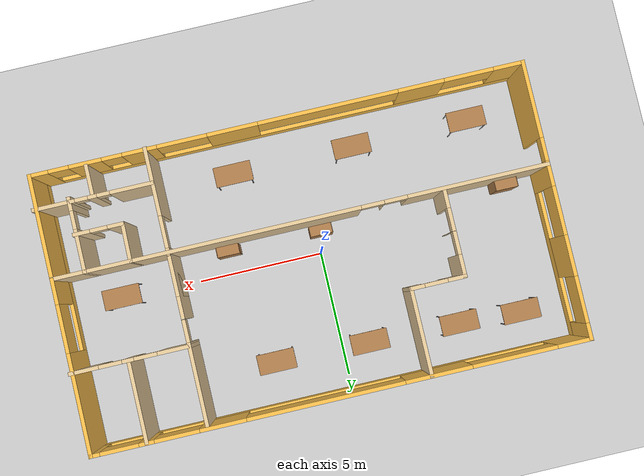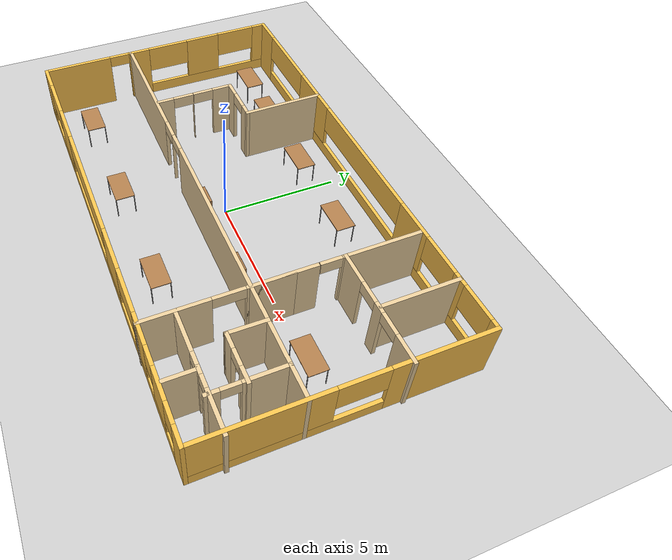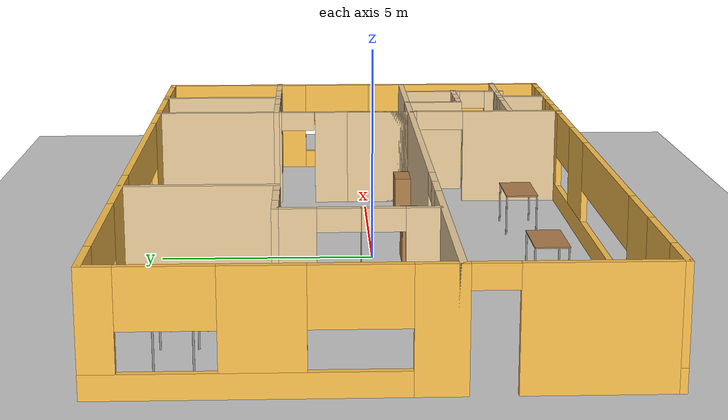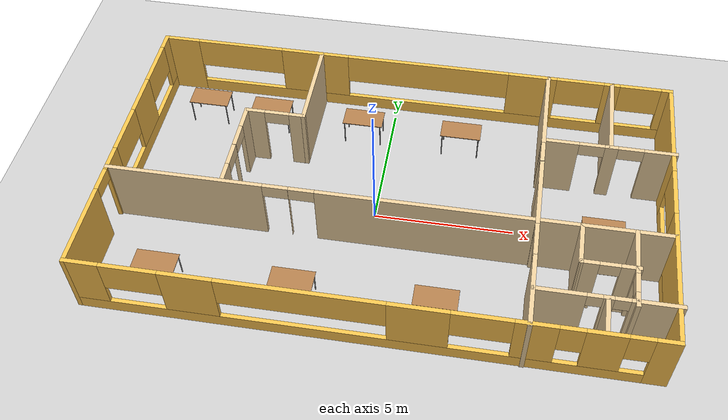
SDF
<sdf version="1.6">
 <world name="default">
  <light name="sun" type="directional">
   <pose>0 0 10 0 -0 0</pose>
   <diffuse>0.8 0.8 0.8 1</diffuse>
   <specular>0.2 0.2 0.2 1</specular>
   <attenuation>
    <range>1000</range>
    <constant>0.9</constant>
    <linear>0.01</linear>
    <quadratic>0.001</quadratic>
   </attenuation>
   <direction>-0.5 0.1 -0.9</direction>
  </light>
  <model name="ground_plane">
   <static>1</static>
   <link name="link">
    <collision name="collision">
     <geometry><plane><normal>0 0 1</normal><size>100 100</size></plane></geometry>
     <surface>
      <contact><collide_bitmask>65535</collide_bitmask></contact>
      <friction><ode><mu>100</mu><mu2>50</mu2></ode></friction>
     </surface>
    </collision>
    <visual name="visual">
     <cast_shadows>0</cast_shadows>
     <geometry><plane><normal>0 0 1</normal><size>100 100</size></plane></geometry>
     <material>
      <script><uri>file://media/materials/scripts/gazebo.material</uri><name>Gazebo/Grey</name></script>
     </material>
    </visual>
   </link>
  </model>
  <gravity>0 0 -9.8</gravity>
  <magnetic_field>6e-06 2.3e-05 -4.2e-05</magnetic_field>
  <atmosphere type="adiabatic"/>
  <physics name="default_physics" default="0" type="ode">
   <max_step_size>0.001</max_step_size>
   <real_time_factor>1</real_time_factor>
   <real_time_update_rate>1000</real_time_update_rate>
  </physics>
  <scene><ambient>0.4 0.4 0.4 1</ambient><background>0.7 0.7 0.7 1</background><shadows>1</shadows></scene>
  <spherical_coordinates>
   <surface_model>EARTH_WGS84</surface_model>
   <latitude_deg>0</latitude_deg>
   <longitude_deg>0</longitude_deg>
   <elevation>0</elevation>
   <heading_deg>0</heading_deg>
  </spherical_coordinates>
  <model name="Untitled">
   <pose>0.58941 0.12908 0 0 -0 0</pose>
   <link name="Wall_10">
    <collision name="Wall_10_Collision">
     <geometry><box><size>3.5 0.15 2.5</size></box></geometry>
     <pose>0 0 1.25 0 -0 0</pose>
    </collision>
    <visual name="Wall_10_Visual">
     <pose>0 0 1.25 0 -0 0</pose>
     <geometry><box><size>3.5 0.15 2.5</size></box></geometry>
     <material>
      <script><uri>file://media/materials/scripts/gazebo.material</uri><name>Gazebo/Grey</name></script>
      <ambient>0.921569 0.807843 0.615686 1</ambient>
     </material>
     <meta><layer>0</layer></meta>
    </visual>
    <pose>-3.5542 3.7347 0 0 0 -1.5708</pose>
   </link>
   <link name="Wall_11">
    <pose>-4.6042 2.05971 0 0 -0 3.14159</pose>
    <visual name="Wall_11_Visual_0">
     <pose>-0.823056 0 1.25 0 -0 0</pose>
     <geometry><box><size>0.603887 0.15 2.5</size></box></geometry>
     <material>
      <script><uri>file://media/materials/scripts/gazebo.material</uri><name>Gazebo/Grey</name></script>
      <ambient>0.921569 0.807843 0.615686 1</ambient>
     </material>
     <meta><layer>0</layer></meta>
    </visual>
    <collision name="Wall_11_Collision_0">
     <geometry><box><size>0.603887 0.15 2.5</size></box></geometry>
     <pose>-0.823056 0 1.25 0 -0 0</pose>
    </collision>
    <visual name="Wall_11_Visual_1">
     <pose>0.751944 0 1.25 0 -0 0</pose>
     <geometry><box><size>0.746113 0.15 2.5</size></box></geometry>
     <material>
      <script><uri>file://media/materials/scripts/gazebo.material</uri><name>Gazebo/Grey</name></script>
      <ambient>0.921569 0.807843 0.615686 1</ambient>
     </material>
     <meta><layer>0</layer></meta>
    </visual>
    <collision name="Wall_11_Collision_1">
     <geometry><box><size>0.746113 0.15 2.5</size></box></geometry>
     <pose>0.751944 0 1.25 0 -0 0</pose>
    </collision>
    <visual name="Wall_11_Visual_2">
     <pose>-0.071113 0 2.25 0 -0 0</pose>
     <geometry><box><size>0.9 0.15 0.5</size></box></geometry>
     <material>
      <script><uri>file://media/materials/scripts/gazebo.material</uri><name>Gazebo/Grey</name></script>
      <ambient>0.921569 0.807843 0.615686 1</ambient>
     </material>
     <meta><layer>0</layer></meta>
    </visual>
    <collision name="Wall_11_Collision_2">
     <geometry><box><size>0.9 0.15 0.5</size></box></geometry>
     <pose>-0.071113 0 2.25 0 -0 0</pose>
    </collision>
   </link>
   <link name="Wall_14">
    <pose>-5.6542 0.384705 0 0 0 -1.5708</pose>
    <visual name="Wall_14_Visual_0">
     <pose>-1.28764 0 1.25 0 -0 0</pose>
     <geometry><box><size>0.924715 0.15 2.5</size></box></geometry>
     <material>
      <script><uri>file://media/materials/scripts/gazebo.material</uri><name>Gazebo/Grey</name></script>
      <ambient>0.921569 0.807843 0.615686 1</ambient>
     </material>
     <meta><layer>0</layer></meta>
    </visual>
    <collision name="Wall_14_Collision_0">
     <geometry><box><size>0.924715 0.15 2.5</size></box></geometry>
     <pose>-1.28764 0 1.25 0 -0 0</pose>
    </collision>
    <visual name="Wall_14_Visual_1">
     <pose>0.083568 0 1.25 0 -0 0</pose>
     <geometry><box><size>0.017707 0.15 2.5</size></box></geometry>
     <material>
      <script><uri>file://media/materials/scripts/gazebo.material</uri><name>Gazebo/Grey</name></script>
      <ambient>0.921569 0.807843 0.615686 1</ambient>
     </material>
     <meta><layer>0</layer></meta>
    </visual>
    <collision name="Wall_14_Collision_1">
     <geometry><box><size>0.017707 0.15 2.5</size></box></geometry>
     <pose>0.083568 0 1.25 0 -0 0</pose>
    </collision>
    <visual name="Wall_14_Visual_2">
     <pose>1.37121 0 1.25 0 -0 0</pose>
     <geometry><box><size>0.757578 0.15 2.5</size></box></geometry>
     <material>
      <script><uri>file://media/materials/scripts/gazebo.material</uri><name>Gazebo/Grey</name></script>
      <ambient>0.921569 0.807843 0.615686 1</ambient>
     </material>
     <meta><layer>0</layer></meta>
    </visual>
    <collision name="Wall_14_Collision_2">
     <geometry><box><size>0.757578 0.15 2.5</size></box></geometry>
     <pose>1.37121 0 1.25 0 -0 0</pose>
    </collision>
    <visual name="Wall_14_Visual_3">
     <pose>-0.375285 0 2.25 0 -0 0</pose>
     <geometry><box><size>0.9 0.15 0.5</size></box></geometry>
     <material>
      <script><uri>file://media/materials/scripts/gazebo.material</uri><name>Gazebo/Grey</name></script>
      <ambient>0.921569 0.807843 0.615686 1</ambient>
     </material>
     <meta><layer>0</layer></meta>
    </visual>
    <collision name="Wall_14_Collision_3">
     <geometry><box><size>0.9 0.15 0.5</size></box></geometry>
     <pose>-0.375285 0 2.25 0 -0 0</pose>
    </collision>
    <visual name="Wall_14_Visual_4">
     <pose>0.542422 0 2.25 0 -0 0</pose>
     <geometry><box><size>0.9 0.15 0.5</size></box></geometry>
     <material>
      <script><uri>file://media/materials/scripts/gazebo.material</uri><name>Gazebo/Grey</name></script>
      <ambient>0.921569 0.807843 0.615686 1</ambient>
     </material>
     <meta><layer>0</layer></meta>
    </visual>
    <collision name="Wall_14_Collision_4">
     <geometry><box><size>0.9 0.15 0.5</size></box></geometry>
     <pose>0.542422 0 2.25 0 -0 0</pose>
    </collision>
   </link>
   <link name="Wall_16">
    <pose>9.61657 0.015295 0 0 0 -1.5708</pose>
    <visual name="Wall_16_Visual_0">
     <pose>-3.48747 0 1.25 0 -0 0</pose>
     <geometry><box><size>4.02505 0.15 2.5</size></box></geometry>
     <material>
      <script><uri>file://media/materials/scripts/gazebo.material</uri><name>Gazebo/Grey</name></script>
      <ambient>1 0.764706 0.305882 1</ambient>
     </material>
     <meta><layer>0</layer></meta>
    </visual>
    <collision name="Wall_16_Collision_0">
     <geometry><box><size>4.02505 0.15 2.5</size></box></geometry>
     <pose>-3.48747 0 1.25 0 -0 0</pose>
    </collision>
    <visual name="Wall_16_Visual_1">
     <pose>2.01253 0 0.25 0 -0 0</pose>
     <geometry><box><size>6.97495 0.15 0.5</size></box></geometry>
     <material>
      <script><uri>file://media/materials/scripts/gazebo.material</uri><name>Gazebo/Grey</name></script>
      <ambient>1 0.764706 0.305882 1</ambient>
     </material>
     <meta><layer>0</layer></meta>
    </visual>
    <collision name="Wall_16_Collision_1">
     <geometry><box><size>6.97495 0.15 0.5</size></box></geometry>
     <pose>2.01253 0 0.25 0 -0 0</pose>
    </collision>
    <visual name="Wall_16_Visual_2">
     <pose>2.95609 0 1.5 0 -0 0</pose>
     <geometry><box><size>5.08781 0.15 2</size></box></geometry>
     <material>
      <script><uri>file://media/materials/scripts/gazebo.material</uri><name>Gazebo/Grey</name></script>
      <ambient>1 0.764706 0.305882 1</ambient>
     </material>
     <meta><layer>0</layer></meta>
    </visual>
    <collision name="Wall_16_Collision_2">
     <geometry><box><size>5.08781 0.15 2</size></box></geometry>
     <pose>2.95609 0 1.5 0 -0 0</pose>
    </collision>
    <visual name="Wall_16_Visual_3">
     <pose>-0.531379 0 1.9 0 -0 0</pose>
     <geometry><box><size>1.88714 0.15 1.2</size></box></geometry>
     <material>
      <script><uri>file://media/materials/scripts/gazebo.material</uri><name>Gazebo/Grey</name></script>
      <ambient>1 0.764706 0.305882 1</ambient>
     </material>
     <meta><layer>0</layer></meta>
    </visual>
    <collision name="Wall_16_Collision_3">
     <geometry><box><size>1.88714 0.15 1.2</size></box></geometry>
     <pose>-0.531379 0 1.9 0 -0 0</pose>
    </collision>
   </link>
   <link name="Wall_17">
    <pose>-0.058425 -5.4097 0 0 -0 3.14159</pose>
    <visual name="Wall_17_Visual_0">
     <pose>-9.34664 0 1.25 0 -0 0</pose>
     <geometry><box><size>0.806721 0.15 2.5</size></box></geometry>
     <material>
      <script><uri>file://media/materials/scripts/gazebo.material</uri><name>Gazebo/Grey</name></script>
      <ambient>1 0.764706 0.305882 1</ambient>
     </material>
     <meta><layer>0</layer></meta>
    </visual>
    <collision name="Wall_17_Collision_0">
     <geometry><box><size>0.806721 0.15 2.5</size></box></geometry>
     <pose>-9.34664 0 1.25 0 -0 0</pose>
    </collision>
    <visual name="Wall_17_Visual_1">
     <pose>0.403361 0 0.25 0 -0 0</pose>
     <geometry><box><size>18.6933 0.15 0.5</size></box></geometry>
     <material>
      <script><uri>file://media/materials/scripts/gazebo.material</uri><name>Gazebo/Grey</name></script>
      <ambient>1 0.764706 0.305882 1</ambient>
     </material>
     <meta><layer>0</layer></meta>
    </visual>
    <collision name="Wall_17_Collision_1">
     <geometry><box><size>18.6933 0.15 0.5</size></box></geometry>
     <pose>0.403361 0 0.25 0 -0 0</pose>
    </collision>
    <visual name="Wall_17_Visual_2">
     <pose>-7.5024 0 1.5 0 -0 0</pose>
     <geometry><box><size>1.28175 0.15 2</size></box></geometry>
     <material>
      <script><uri>file://media/materials/scripts/gazebo.material</uri><name>Gazebo/Grey</name></script>
      <ambient>1 0.764706 0.305882 1</ambient>
     </material>
     <meta><layer>0</layer></meta>
    </visual>
    <collision name="Wall_17_Collision_2">
     <geometry><box><size>1.28175 0.15 2</size></box></geometry>
     <pose>-7.5024 0 1.5 0 -0 0</pose>
    </collision>
    <visual name="Wall_17_Visual_3">
     <pose>-5.38313 0 1.5 0 -0 0</pose>
     <geometry><box><size>1.35679 0.15 2</size></box></geometry>
     <material>
      <script><uri>file://media/materials/scripts/gazebo.material</uri><name>Gazebo/Grey</name></script>
      <ambient>1 0.764706 0.305882 1</ambient>
     </material>
     <meta><layer>0</layer></meta>
    </visual>
    <collision name="Wall_17_Collision_3">
     <geometry><box><size>1.35679 0.15 2</size></box></geometry>
     <pose>-5.38313 0 1.5 0 -0 0</pose>
    </collision>
    <visual name="Wall_17_Visual_4">
     <pose>-1.74867 0 1.5 0 -0 0</pose>
     <geometry><box><size>1.98726 0.15 2</size></box></geometry>
     <material>
      <script><uri>file://media/materials/scripts/gazebo.material</uri><name>Gazebo/Grey</name></script>
      <ambient>1 0.764706 0.305882 1</ambient>
     </material>
     <meta><layer>0</layer></meta>
    </visual>
    <collision name="Wall_17_Collision_4">
     <geometry><box><size>1.98726 0.15 2</size></box></geometry>
     <pose>-1.74867 0 1.5 0 -0 0</pose>
    </collision>
    <visual name="Wall_17_Visual_5">
     <pose>5.67048 0 1.5 0 -0 0</pose>
     <geometry><box><size>1.81376 0.15 2</size></box></geometry>
     <material>
      <script><uri>file://media/materials/scripts/gazebo.material</uri><name>Gazebo/Grey</name></script>
      <ambient>1 0.764706 0.305882 1</ambient>
     </material>
     <meta><layer>0</layer></meta>
    </visual>
    <collision name="Wall_17_Collision_5">
     <geometry><box><size>1.81376 0.15 2</size></box></geometry>
     <pose>5.67048 0 1.5 0 -0 0</pose>
    </collision>
    <visual name="Wall_17_Visual_6">
     <pose>9.13038 0 1.5 0 -0 0</pose>
     <geometry><box><size>1.23924 0.15 2</size></box></geometry>
     <material>
      <script><uri>file://media/materials/scripts/gazebo.material</uri><name>Gazebo/Grey</name></script>
      <ambient>1 0.764706 0.305882 1</ambient>
     </material>
     <meta><layer>0</layer></meta>
    </visual>
    <collision name="Wall_17_Collision_6">
     <geometry><box><size>1.23924 0.15 2</size></box></geometry>
     <pose>9.13038 0 1.5 0 -0 0</pose>
    </collision>
    <visual name="Wall_17_Visual_7">
     <pose>-8.54328 0 1.9 0 -0 0</pose>
     <geometry><box><size>0.8 0.15 1.2</size></box></geometry>
     <material>
      <script><uri>file://media/materials/scripts/gazebo.material</uri><name>Gazebo/Grey</name></script>
      <ambient>1 0.764706 0.305882 1</ambient>
     </material>
     <meta><layer>0</layer></meta>
    </visual>
    <collision name="Wall_17_Collision_7">
     <geometry><box><size>0.8 0.15 1.2</size></box></geometry>
     <pose>-8.54328 0 1.9 0 -0 0</pose>
    </collision>
    <visual name="Wall_17_Visual_8">
     <pose>-6.46152 0 1.9 0 -0 0</pose>
     <geometry><box><size>0.8 0.15 1.2</size></box></geometry>
     <material>
      <script><uri>file://media/materials/scripts/gazebo.material</uri><name>Gazebo/Grey</name></script>
      <ambient>1 0.764706 0.305882 1</ambient>
     </material>
     <meta><layer>0</layer></meta>
    </visual>
    <collision name="Wall_17_Collision_8">
     <geometry><box><size>0.8 0.15 1.2</size></box></geometry>
     <pose>-6.46152 0 1.9 0 -0 0</pose>
    </collision>
    <visual name="Wall_17_Visual_9">
     <pose>-3.72352 0 1.9 0 -0 0</pose>
     <geometry><box><size>1.96243 0.15 1.2</size></box></geometry>
     <material>
      <script><uri>file://media/materials/scripts/gazebo.material</uri><name>Gazebo/Grey</name></script>
      <ambient>1 0.764706 0.305882 1</ambient>
     </material>
     <meta><layer>0</layer></meta>
    </visual>
    <collision name="Wall_17_Collision_9">
     <geometry><box><size>1.96243 0.15 1.2</size></box></geometry>
     <pose>-3.72352 0 1.9 0 -0 0</pose>
    </collision>
    <visual name="Wall_17_Visual_10">
     <pose>2.00428 0 1.9 0 -0 0</pose>
     <geometry><box><size>5.51864 0.15 1.2</size></box></geometry>
     <material>
      <script><uri>file://media/materials/scripts/gazebo.material</uri><name>Gazebo/Grey</name></script>
      <ambient>1 0.764706 0.305882 1</ambient>
     </material>
     <meta><layer>0</layer></meta>
    </visual>
    <collision name="Wall_17_Collision_10">
     <geometry><box><size>5.51864 0.15 1.2</size></box></geometry>
     <pose>2.00428 0 1.9 0 -0 0</pose>
    </collision>
    <visual name="Wall_17_Visual_11">
     <pose>7.54406 0 1.9 0 -0 0</pose>
     <geometry><box><size>1.9334 0.15 1.2</size></box></geometry>
     <material>
      <script><uri>file://media/materials/scripts/gazebo.material</uri><name>Gazebo/Grey</name></script>
      <ambient>1 0.764706 0.305882 1</ambient>
     </material>
     <meta><layer>0</layer></meta>
    </visual>
    <collision name="Wall_17_Collision_11">
     <geometry><box><size>1.9334 0.15 1.2</size></box></geometry>
     <pose>7.54406 0 1.9 0 -0 0</pose>
    </collision>
   </link>
   <link name="Wall_18">
    <pose>-9.73343 0.015295 0 0 -0 1.5708</pose>
    <visual name="Wall_18_Visual_0">
     <pose>-3.96666 0 1.25 0 -0 0</pose>
     <geometry><box><size>3.06668 0.15 2.5</size></box></geometry>
     <material>
      <script><uri>file://media/materials/scripts/gazebo.material</uri><name>Gazebo/Grey</name></script>
      <ambient>1 0.764706 0.305882 1</ambient>
     </material>
     <meta><layer>0</layer></meta>
    </visual>
    <collision name="Wall_18_Collision_0">
     <geometry><box><size>3.06668 0.15 2.5</size></box></geometry>
     <pose>-3.96666 0 1.25 0 -0 0</pose>
    </collision>
    <visual name="Wall_18_Visual_1">
     <pose>-1.03058 0 1.25 0 -0 0</pose>
     <geometry><box><size>1.00548 0.15 2.5</size></box></geometry>
     <material>
      <script><uri>file://media/materials/scripts/gazebo.material</uri><name>Gazebo/Grey</name></script>
      <ambient>1 0.764706 0.305882 1</ambient>
     </material>
     <meta><layer>0</layer></meta>
    </visual>
    <collision name="Wall_18_Collision_1">
     <geometry><box><size>1.00548 0.15 2.5</size></box></geometry>
     <pose>-1.03058 0 1.25 0 -0 0</pose>
    </collision>
    <visual name="Wall_18_Visual_2">
     <pose>2.48608 0 0.25 0 -0 0</pose>
     <geometry><box><size>6.02784 0.15 0.5</size></box></geometry>
     <material>
      <script><uri>file://media/materials/scripts/gazebo.material</uri><name>Gazebo/Grey</name></script>
      <ambient>1 0.764706 0.305882 1</ambient>
     </material>
     <meta><layer>0</layer></meta>
    </visual>
    <collision name="Wall_18_Collision_2">
     <geometry><box><size>6.02784 0.15 0.5</size></box></geometry>
     <pose>2.48608 0 0.25 0 -0 0</pose>
    </collision>
    <visual name="Wall_18_Visual_3">
     <pose>2.18522 0 1.5 0 -0 0</pose>
     <geometry><box><size>1.60558 0.15 2</size></box></geometry>
     <material>
      <script><uri>file://media/materials/scripts/gazebo.material</uri><name>Gazebo/Grey</name></script>
      <ambient>1 0.764706 0.305882 1</ambient>
     </material>
     <meta><layer>0</layer></meta>
    </visual>
    <collision name="Wall_18_Collision_3">
     <geometry><box><size>1.60558 0.15 2</size></box></geometry>
     <pose>2.18522 0 1.5 0 -0 0</pose>
    </collision>
    <visual name="Wall_18_Visual_4">
     <pose>5.15288 0 1.5 0 -0 0</pose>
     <geometry><box><size>0.694244 0.15 2</size></box></geometry>
     <material>
      <script><uri>file://media/materials/scripts/gazebo.material</uri><name>Gazebo/Grey</name></script>
      <ambient>1 0.764706 0.305882 1</ambient>
     </material>
     <meta><layer>0</layer></meta>
    </visual>
    <collision name="Wall_18_Collision_4">
     <geometry><box><size>0.694244 0.15 2</size></box></geometry>
     <pose>5.15288 0 1.5 0 -0 0</pose>
    </collision>
    <visual name="Wall_18_Visual_5">
     <pose>0.427291 0 1.9 0 -0 0</pose>
     <geometry><box><size>1.91027 0.15 1.2</size></box></geometry>
     <material>
      <script><uri>file://media/materials/scripts/gazebo.material</uri><name>Gazebo/Grey</name></script>
      <ambient>1 0.764706 0.305882 1</ambient>
     </material>
     <meta><layer>0</layer></meta>
    </visual>
    <collision name="Wall_18_Collision_5">
     <geometry><box><size>1.91027 0.15 1.2</size></box></geometry>
     <pose>0.427291 0 1.9 0 -0 0</pose>
    </collision>
    <visual name="Wall_18_Visual_6">
     <pose>3.89688 0 1.9 0 -0 0</pose>
     <geometry><box><size>1.81775 0.15 1.2</size></box></geometry>
     <material>
      <script><uri>file://media/materials/scripts/gazebo.material</uri><name>Gazebo/Grey</name></script>
      <ambient>1 0.764706 0.305882 1</ambient>
     </material>
     <meta><layer>0</layer></meta>
    </visual>
    <collision name="Wall_18_Collision_6">
     <geometry><box><size>1.81775 0.15 1.2</size></box></geometry>
     <pose>3.89688 0 1.9 0 -0 0</pose>
    </collision>
    <visual name="Wall_18_Visual_7">
     <pose>-1.98332 0 2.25 0 -0 0</pose>
     <geometry><box><size>0.9 0.15 0.5</size></box></geometry>
     <material>
      <script><uri>file://media/materials/scripts/gazebo.material</uri><name>Gazebo/Grey</name></script>
      <ambient>1 0.764706 0.305882 1</ambient>
     </material>
     <meta><layer>0</layer></meta>
    </visual>
    <collision name="Wall_18_Collision_7">
     <geometry><box><size>0.9 0.15 0.5</size></box></geometry>
     <pose>-1.98332 0 2.25 0 -0 0</pose>
    </collision>
   </link>
   <link name="Wall_20">
    <pose>-0.058425 -1.38133 0 0 -0 0</pose>
    <visual name="Wall_20_Visual_0">
     <pose>-6.96126 0 1.25 0 -0 0</pose>
     <geometry><box><size>5.57748 0.15 2.5</size></box></geometry>
     <material>
      <script><uri>file://media/materials/scripts/gazebo.material</uri><name>Gazebo/Grey</name></script>
      <ambient>0.921569 0.807843 0.615686 1</ambient>
     </material>
     <meta><layer>0</layer></meta>
    </visual>
    <collision name="Wall_20_Collision_0">
     <geometry><box><size>5.57748 0.15 2.5</size></box></geometry>
     <pose>-6.96126 0 1.25 0 -0 0</pose>
    </collision>
    <visual name="Wall_20_Visual_1">
     <pose>-3.26996 0 1.25 0 -0 0</pose>
     <geometry><box><size>0.005111 0.15 2.5</size></box></geometry>
     <material>
      <script><uri>file://media/materials/scripts/gazebo.material</uri><name>Gazebo/Grey</name></script>
      <ambient>0.921569 0.807843 0.615686 1</ambient>
     </material>
     <meta><layer>0</layer></meta>
    </visual>
    <collision name="Wall_20_Collision_1">
     <geometry><box><size>0.005111 0.15 2.5</size></box></geometry>
     <pose>-3.26996 0 1.25 0 -0 0</pose>
    </collision>
    <visual name="Wall_20_Visual_2">
     <pose>3.6913 0 1.25 0 -0 0</pose>
     <geometry><box><size>12.1174 0.15 2.5</size></box></geometry>
     <material>
      <script><uri>file://media/materials/scripts/gazebo.material</uri><name>Gazebo/Grey</name></script>
      <ambient>0.921569 0.807843 0.615686 1</ambient>
     </material>
     <meta><layer>0</layer></meta>
    </visual>
    <collision name="Wall_20_Collision_2">
     <geometry><box><size>12.1174 0.15 2.5</size></box></geometry>
     <pose>3.6913 0 1.25 0 -0 0</pose>
    </collision>
    <visual name="Wall_20_Visual_3">
     <pose>-3.72252 0 2.25 0 -0 0</pose>
     <geometry><box><size>0.9 0.15 0.5</size></box></geometry>
     <material>
      <script><uri>file://media/materials/scripts/gazebo.material</uri><name>Gazebo/Grey</name></script>
      <ambient>0.921569 0.807843 0.615686 1</ambient>
     </material>
     <meta><layer>0</layer></meta>
    </visual>
    <collision name="Wall_20_Collision_3">
     <geometry><box><size>0.9 0.15 0.5</size></box></geometry>
     <pose>-3.72252 0 2.25 0 -0 0</pose>
    </collision>
    <visual name="Wall_20_Visual_4">
     <pose>-2.81741 0 2.25 0 -0 0</pose>
     <geometry><box><size>0.9 0.15 0.5</size></box></geometry>
     <material>
      <script><uri>file://media/materials/scripts/gazebo.material</uri><name>Gazebo/Grey</name></script>
      <ambient>0.921569 0.807843 0.615686 1</ambient>
     </material>
     <meta><layer>0</layer></meta>
    </visual>
    <collision name="Wall_20_Collision_4">
     <geometry><box><size>0.9 0.15 0.5</size></box></geometry>
     <pose>-2.81741 0 2.25 0 -0 0</pose>
    </collision>
   </link>
   <link name="Wall_22">
    <pose>5.10284 -0.015295 0 0 0 -1.5708</pose>
    <visual name="Wall_22_Visual_0">
     <pose>-3.8169 0 1.25 0 -0 0</pose>
     <geometry><box><size>3.3662 0.15 2.5</size></box></geometry>
     <material>
      <script><uri>file://media/materials/scripts/gazebo.material</uri><name>Gazebo/Grey</name></script>
      <ambient>0.921569 0.807843 0.615686 1</ambient>
     </material>
     <meta><layer>0</layer></meta>
    </visual>
    <collision name="Wall_22_Collision_0">
     <geometry><box><size>3.3662 0.15 2.5</size></box></geometry>
     <pose>-3.8169 0 1.25 0 -0 0</pose>
    </collision>
    <visual name="Wall_22_Visual_1">
     <pose>0.14955 0 1.25 0 -0 0</pose>
     <geometry><box><size>2.76671 0.15 2.5</size></box></geometry>
     <material>
      <script><uri>file://media/materials/scripts/gazebo.material</uri><name>Gazebo/Grey</name></script>
      <ambient>0.921569 0.807843 0.615686 1</ambient>
     </material>
     <meta><layer>0</layer></meta>
    </visual>
    <collision name="Wall_22_Collision_1">
     <geometry><box><size>2.76671 0.15 2.5</size></box></geometry>
     <pose>0.14955 0 1.25 0 -0 0</pose>
    </collision>
    <visual name="Wall_22_Visual_2">
     <pose>0.589031 0 1.25 0 -0 0</pose>
     <geometry><box><size>1.88774 0.15 2.5</size></box></geometry>
     <material>
      <script><uri>file://media/materials/scripts/gazebo.material</uri><name>Gazebo/Grey</name></script>
      <ambient>0.921569 0.807843 0.615686 1</ambient>
     </material>
     <meta><layer>0</layer></meta>
    </visual>
    <collision name="Wall_22_Collision_2">
     <geometry><box><size>1.88774 0.15 2.5</size></box></geometry>
     <pose>0.589031 0 1.25 0 -0 0</pose>
    </collision>
    <visual name="Wall_22_Visual_3">
     <pose>4.14747 0 1.25 0 -0 0</pose>
     <geometry><box><size>2.70505 0.15 2.5</size></box></geometry>
     <material>
      <script><uri>file://media/materials/scripts/gazebo.material</uri><name>Gazebo/Grey</name></script>
      <ambient>0.921569 0.807843 0.615686 1</ambient>
     </material>
     <meta><layer>0</layer></meta>
    </visual>
    <collision name="Wall_22_Collision_3">
     <geometry><box><size>2.70505 0.15 2.5</size></box></geometry>
     <pose>4.14747 0 1.25 0 -0 0</pose>
    </collision>
    <visual name="Wall_22_Visual_4">
     <pose>-1.69432 0 2.25 0 -0 0</pose>
     <geometry><box><size>0.878963 0.15 0.5</size></box></geometry>
     <material>
      <script><uri>file://media/materials/scripts/gazebo.material</uri><name>Gazebo/Grey</name></script>
      <ambient>0.921569 0.807843 0.615686 1</ambient>
     </material>
     <meta><layer>0</layer></meta>
    </visual>
    <collision name="Wall_22_Collision_4">
     <geometry><box><size>0.878963 0.15 0.5</size></box></geometry>
     <pose>-1.69432 0 2.25 0 -0 0</pose>
    </collision>
    <visual name="Wall_22_Visual_5">
     <pose>2.16392 0 2.25 0 -0 0</pose>
     <geometry><box><size>1.26204 0.15 0.5</size></box></geometry>
     <material>
      <script><uri>file://media/materials/scripts/gazebo.material</uri><name>Gazebo/Grey</name></script>
      <ambient>0.921569 0.807843 0.615686 1</ambient>
     </material>
     <meta><layer>0</layer></meta>
    </visual>
    <collision name="Wall_22_Collision_5">
     <geometry><box><size>1.26204 0.15 0.5</size></box></geometry>
     <pose>2.16392 0 2.25 0 -0 0</pose>
    </collision>
    <visual name="Wall_22_Visual_6">
     <pose>2.16392 0 2.25 0 -0 0</pose>
     <geometry><box><size>1.26204 0.15 0.5</size></box></geometry>
     <material>
      <script><uri>file://media/materials/scripts/gazebo.material</uri><name>Gazebo/Grey</name></script>
      <ambient>0.921569 0.807843 0.615686 1</ambient>
     </material>
     <meta><layer>0</layer></meta>
    </visual>
    <collision name="Wall_22_Collision_6">
     <geometry><box><size>1.26204 0.15 0.5</size></box></geometry>
     <pose>2.16392 0 2.25 0 -0 0</pose>
    </collision>
   </link>
   <link name="Wall_24">
    <pose>7.40284 2.25891 0 0 -0 0</pose>
    <visual name="Wall_24_Visual_0">
     <pose>-1.71576 0 1.25 0 -0 0</pose>
     <geometry><box><size>1.31848 0.15 2.5</size></box></geometry>
     <material>
      <script><uri>file://media/materials/scripts/gazebo.material</uri><name>Gazebo/Grey</name></script>
      <ambient>0.921569 0.807843 0.615686 1</ambient>
     </material>
     <meta><layer>0</layer></meta>
    </visual>
    <collision name="Wall_24_Collision_0">
     <geometry><box><size>1.31848 0.15 2.5</size></box></geometry>
     <pose>-1.71576 0 1.25 0 -0 0</pose>
    </collision>
    <visual name="Wall_24_Visual_1">
     <pose>0.075836 0 1.25 0 -0 0</pose>
     <geometry><box><size>0.464706 0.15 2.5</size></box></geometry>
     <material>
      <script><uri>file://media/materials/scripts/gazebo.material</uri><name>Gazebo/Grey</name></script>
      <ambient>0.921569 0.807843 0.615686 1</ambient>
     </material>
     <meta><layer>0</layer></meta>
    </visual>
    <collision name="Wall_24_Collision_1">
     <geometry><box><size>0.464706 0.15 2.5</size></box></geometry>
     <pose>0.075836 0 1.25 0 -0 0</pose>
    </collision>
    <visual name="Wall_24_Visual_2">
     <pose>1.7916 0 1.25 0 -0 0</pose>
     <geometry><box><size>1.16681 0.15 2.5</size></box></geometry>
     <material>
      <script><uri>file://media/materials/scripts/gazebo.material</uri><name>Gazebo/Grey</name></script>
      <ambient>0.921569 0.807843 0.615686 1</ambient>
     </material>
     <meta><layer>0</layer></meta>
    </visual>
    <collision name="Wall_24_Collision_2">
     <geometry><box><size>1.16681 0.15 2.5</size></box></geometry>
     <pose>1.7916 0 1.25 0 -0 0</pose>
    </collision>
    <visual name="Wall_24_Visual_3">
     <pose>-0.606517 0 2.25 0 -0 0</pose>
     <geometry><box><size>0.9 0.15 0.5</size></box></geometry>
     <material>
      <script><uri>file://media/materials/scripts/gazebo.material</uri><name>Gazebo/Grey</name></script>
      <ambient>0.921569 0.807843 0.615686 1</ambient>
     </material>
     <meta><layer>0</layer></meta>
    </visual>
    <collision name="Wall_24_Collision_3">
     <geometry><box><size>0.9 0.15 0.5</size></box></geometry>
     <pose>-0.606517 0 2.25 0 -0 0</pose>
    </collision>
    <visual name="Wall_24_Visual_4">
     <pose>0.758189 0 2.25 0 -0 0</pose>
     <geometry><box><size>0.9 0.15 0.5</size></box></geometry>
     <material>
      <script><uri>file://media/materials/scripts/gazebo.material</uri><name>Gazebo/Grey</name></script>
      <ambient>0.921569 0.807843 0.615686 1</ambient>
     </material>
     <meta><layer>0</layer></meta>
    </visual>
    <collision name="Wall_24_Collision_4">
     <geometry><box><size>0.9 0.15 0.5</size></box></geometry>
     <pose>0.758189 0 2.25 0 -0 0</pose>
    </collision>
   </link>
   <link name="Wall_26">
    <collision name="Wall_26_Collision">
     <geometry><box><size>3.25 0.15 2.5</size></box></geometry>
     <pose>0 0 1.25 0 -0 0</pose>
    </collision>
    <visual name="Wall_26_Visual">
     <pose>0 0 1.25 0 -0 0</pose>
     <geometry><box><size>3.25 0.15 2.5</size></box></geometry>
     <material>
      <script><uri>file://media/materials/scripts/gazebo.material</uri><name>Gazebo/Grey</name></script>
      <ambient>0.921569 0.807843 0.615686 1</ambient>
     </material>
     <meta><layer>0</layer></meta>
    </visual>
    <pose>7.45828 3.8597 0 0 0 -1.5708</pose>
   </link>
   <link name="Wall_28">
    <pose>7.43343 -4.10386 0 0 -0 0</pose>
    <visual name="Wall_28_Visual_0">
     <pose>-1.5171 0 1.25 0 -0 0</pose>
     <geometry><box><size>1.71581 0.15 2.5</size></box></geometry>
     <material>
      <script><uri>file://media/materials/scripts/gazebo.material</uri><name>Gazebo/Grey</name></script>
      <ambient>0.921569 0.807843 0.615686 1</ambient>
     </material>
     <meta><layer>0</layer></meta>
    </visual>
    <collision name="Wall_28_Collision_0">
     <geometry><box><size>1.71581 0.15 2.5</size></box></geometry>
     <pose>-1.5171 0 1.25 0 -0 0</pose>
    </collision>
    <visual name="Wall_28_Visual_1">
     <pose>0.022115 0 1.25 0 -0 0</pose>
     <geometry><box><size>0.349052 0.15 2.5</size></box></geometry>
     <material>
      <script><uri>file://media/materials/scripts/gazebo.material</uri><name>Gazebo/Grey</name></script>
      <ambient>0.921569 0.807843 0.615686 1</ambient>
     </material>
     <meta><layer>0</layer></meta>
    </visual>
    <collision name="Wall_28_Collision_1">
     <geometry><box><size>0.349052 0.15 2.5</size></box></geometry>
     <pose>0.022115 0 1.25 0 -0 0</pose>
    </collision>
    <visual name="Wall_28_Visual_2">
     <pose>1.53921 0 1.25 0 -0 0</pose>
     <geometry><box><size>1.67158 0.15 2.5</size></box></geometry>
     <material>
      <script><uri>file://media/materials/scripts/gazebo.material</uri><name>Gazebo/Grey</name></script>
      <ambient>0.921569 0.807843 0.615686 1</ambient>
     </material>
     <meta><layer>0</layer></meta>
    </visual>
    <collision name="Wall_28_Collision_2">
     <geometry><box><size>1.67158 0.15 2.5</size></box></geometry>
     <pose>1.53921 0 1.25 0 -0 0</pose>
    </collision>
    <visual name="Wall_28_Visual_3">
     <pose>-0.405801 0 2.25 0 -0 0</pose>
     <geometry><box><size>0.50678 0.15 0.5</size></box></geometry>
     <material>
      <script><uri>file://media/materials/scripts/gazebo.material</uri><name>Gazebo/Grey</name></script>
      <ambient>0.921569 0.807843 0.615686 1</ambient>
     </material>
     <meta><layer>0</layer></meta>
    </visual>
    <collision name="Wall_28_Collision_3">
     <geometry><box><size>0.50678 0.15 0.5</size></box></geometry>
     <pose>-0.405801 0 2.25 0 -0 0</pose>
    </collision>
    <visual name="Wall_28_Visual_4">
     <pose>0.450031 0 2.25 0 -0 0</pose>
     <geometry><box><size>0.50678 0.15 0.5</size></box></geometry>
     <material>
      <script><uri>file://media/materials/scripts/gazebo.material</uri><name>Gazebo/Grey</name></script>
      <ambient>0.921569 0.807843 0.615686 1</ambient>
     </material>
     <meta><layer>0</layer></meta>
    </visual>
    <collision name="Wall_28_Collision_4">
     <geometry><box><size>0.50678 0.15 0.5</size></box></geometry>
     <pose>0.450031 0 2.25 0 -0 0</pose>
    </collision>
   </link>
   <link name="Wall_30">
    <pose>8.3454 -2.80633 0 0 0 -1.5708</pose>
    <visual name="Wall_30_Visual_0">
     <pose>-0.634862 0 1.25 0 -0 0</pose>
     <geometry><box><size>1.73028 0.15 2.5</size></box></geometry>
     <material>
      <script><uri>file://media/materials/scripts/gazebo.material</uri><name>Gazebo/Grey</name></script>
      <ambient>0.921569 0.807843 0.615686 1</ambient>
     </material>
     <meta><layer>0</layer></meta>
    </visual>
    <collision name="Wall_30_Collision_0">
     <geometry><box><size>1.73028 0.15 2.5</size></box></geometry>
     <pose>-0.634862 0 1.25 0 -0 0</pose>
    </collision>
    <visual name="Wall_30_Visual_1">
     <pose>1.22463 0 1.25 0 -0 0</pose>
     <geometry><box><size>0.550746 0.15 2.5</size></box></geometry>
     <material>
      <script><uri>file://media/materials/scripts/gazebo.material</uri><name>Gazebo/Grey</name></script>
      <ambient>0.921569 0.807843 0.615686 1</ambient>
     </material>
     <meta><layer>0</layer></meta>
    </visual>
    <collision name="Wall_30_Collision_1">
     <geometry><box><size>0.550746 0.15 2.5</size></box></geometry>
     <pose>1.22463 0 1.25 0 -0 0</pose>
    </collision>
    <visual name="Wall_30_Visual_2">
     <pose>0.589765 0 2.25 0 -0 0</pose>
     <geometry><box><size>0.718978 0.15 0.5</size></box></geometry>
     <material>
      <script><uri>file://media/materials/scripts/gazebo.material</uri><name>Gazebo/Grey</name></script>
      <ambient>0.921569 0.807843 0.615686 1</ambient>
     </material>
     <meta><layer>0</layer></meta>
    </visual>
    <collision name="Wall_30_Collision_2">
     <geometry><box><size>0.718978 0.15 0.5</size></box></geometry>
     <pose>0.589765 0 2.25 0 -0 0</pose>
    </collision>
   </link>
   <link name="Wall_32">
    <collision name="Wall_32_Collision">
     <geometry><box><size>1.60934 0.15 2.5</size></box></geometry>
     <pose>0 0 1.25 0 -0 0</pose>
    </collision>
    <visual name="Wall_32_Visual">
     <pose>0 0 1.25 0 -0 0</pose>
     <geometry><box><size>1.60934 0.15 2.5</size></box></geometry>
     <material>
      <script><uri>file://media/materials/scripts/gazebo.material</uri><name>Gazebo/Grey</name></script>
      <ambient>0.921569 0.807843 0.615686 1</ambient>
     </material>
     <meta><layer>0</layer></meta>
    </visual>
    <pose>6.56111 -2.11093 0 0 0 -1.58458</pose>
   </link>
   <link name="Wall_33">
    <pose>7.49617 -2.84053 0 0 -0 0</pose>
    <visual name="Wall_33_Visual_0">
     <pose>-0.676442 0 1.25 0 -0 0</pose>
     <geometry><box><size>0.647116 0.15 2.5</size></box></geometry>
     <material>
      <script><uri>file://media/materials/scripts/gazebo.material</uri><name>Gazebo/Grey</name></script>
      <ambient>0.921569 0.807843 0.615686 1</ambient>
     </material>
     <meta><layer>0</layer></meta>
    </visual>
    <collision name="Wall_33_Collision_0">
     <geometry><box><size>0.647116 0.15 2.5</size></box></geometry>
     <pose>-0.676442 0 1.25 0 -0 0</pose>
    </collision>
    <visual name="Wall_33_Visual_1">
     <pose>0.662933 0 1.25 0 -0 0</pose>
     <geometry><box><size>0.674133 0.15 2.5</size></box></geometry>
     <material>
      <script><uri>file://media/materials/scripts/gazebo.material</uri><name>Gazebo/Grey</name></script>
      <ambient>0.921569 0.807843 0.615686 1</ambient>
     </material>
     <meta><layer>0</layer></meta>
    </visual>
    <collision name="Wall_33_Collision_1">
     <geometry><box><size>0.674133 0.15 2.5</size></box></geometry>
     <pose>0.662933 0 1.25 0 -0 0</pose>
    </collision>
    <visual name="Wall_33_Visual_2">
     <pose>-0.013509 0 2.25 0 -0 0</pose>
     <geometry><box><size>0.678751 0.15 0.5</size></box></geometry>
     <material>
      <script><uri>file://media/materials/scripts/gazebo.material</uri><name>Gazebo/Grey</name></script>
      <ambient>0.921569 0.807843 0.615686 1</ambient>
     </material>
     <meta><layer>0</layer></meta>
    </visual>
    <collision name="Wall_33_Collision_2">
     <geometry><box><size>0.678751 0.15 0.5</size></box></geometry>
     <pose>-0.013509 0 2.25 0 -0 0</pose>
    </collision>
   </link>
   <link name="Wall_35">
    <collision name="Wall_35_Collision">
     <geometry><box><size>1.25 0.15 2.5</size></box></geometry>
     <pose>0 0 1.25 0 -0 0</pose>
    </collision>
    <visual name="Wall_35_Visual">
     <pose>0 0 1.25 0 -0 0</pose>
     <geometry><box><size>1.25 0.15 2.5</size></box></geometry>
     <material>
      <script><uri>file://media/materials/scripts/gazebo.material</uri><name>Gazebo/Grey</name></script>
      <ambient>0.921569 0.807843 0.615686 1</ambient>
     </material>
     <meta><layer>0</layer></meta>
    </visual>
    <pose>7.42769 -4.74563 0 0 0 -1.5708</pose>
   </link>
   <link name="Wall_5">
    <pose>-0.058425 5.44029 0 0 -0 0</pose>
    <visual name="Wall_5_Visual_0">
     <pose>-9.06099 0 1.25 0 -0 0</pose>
     <geometry><box><size>1.37802 0.15 2.5</size></box></geometry>
     <material>
      <script><uri>file://media/materials/scripts/gazebo.material</uri><name>Gazebo/Grey</name></script>
      <ambient>1 0.764706 0.305882 1</ambient>
     </material>
     <meta><layer>0</layer></meta>
    </visual>
    <collision name="Wall_5_Collision_0">
     <geometry><box><size>1.37802 0.15 2.5</size></box></geometry>
     <pose>-9.06099 0 1.25 0 -0 0</pose>
    </collision>
    <visual name="Wall_5_Visual_1">
     <pose>0.689012 0 0.25 0 -0 0</pose>
     <geometry><box><size>18.122 0.15 0.5</size></box></geometry>
     <material>
      <script><uri>file://media/materials/scripts/gazebo.material</uri><name>Gazebo/Grey</name></script>
      <ambient>1 0.764706 0.305882 1</ambient>
     </material>
     <meta><layer>0</layer></meta>
    </visual>
    <collision name="Wall_5_Collision_1">
     <geometry><box><size>18.122 0.15 0.5</size></box></geometry>
     <pose>0.689012 0 0.25 0 -0 0</pose>
    </collision>
    <visual name="Wall_5_Visual_2">
     <pose>-3.77377 0 1.5 0 -0 0</pose>
     <geometry><box><size>2.6002 0.15 2</size></box></geometry>
     <material>
      <script><uri>file://media/materials/scripts/gazebo.material</uri><name>Gazebo/Grey</name></script>
      <ambient>1 0.764706 0.305882 1</ambient>
     </material>
     <meta><layer>0</layer></meta>
    </visual>
    <collision name="Wall_5_Collision_2">
     <geometry><box><size>2.6002 0.15 2</size></box></geometry>
     <pose>-3.77377 0 1.5 0 -0 0</pose>
    </collision>
    <visual name="Wall_5_Visual_3">
     <pose>4.57482 0 1.5 0 -0 0</pose>
     <geometry><box><size>1.81063 0.15 2</size></box></geometry>
     <material>
      <script><uri>file://media/materials/scripts/gazebo.material</uri><name>Gazebo/Grey</name></script>
      <ambient>1 0.764706 0.305882 1</ambient>
     </material>
     <meta><layer>0</layer></meta>
    </visual>
    <collision name="Wall_5_Collision_3">
     <geometry><box><size>1.81063 0.15 2</size></box></geometry>
     <pose>4.57482 0 1.5 0 -0 0</pose>
    </collision>
    <visual name="Wall_5_Visual_4">
     <pose>7.52436 0 1.5 0 -0 0</pose>
     <geometry><box><size>0.591855 0.15 2</size></box></geometry>
     <material>
      <script><uri>file://media/materials/scripts/gazebo.material</uri><name>Gazebo/Grey</name></script>
      <ambient>1 0.764706 0.305882 1</ambient>
     </material>
     <meta><layer>0</layer></meta>
    </visual>
    <collision name="Wall_5_Collision_4">
     <geometry><box><size>0.591855 0.15 2</size></box></geometry>
     <pose>7.52436 0 1.5 0 -0 0</pose>
    </collision>
    <visual name="Wall_5_Visual_5">
     <pose>9.53693 0 1.5 0 -0 0</pose>
     <geometry><box><size>0.426141 0.15 2</size></box></geometry>
     <material>
      <script><uri>file://media/materials/scripts/gazebo.material</uri><name>Gazebo/Grey</name></script>
      <ambient>1 0.764706 0.305882 1</ambient>
     </material>
     <meta><layer>0</layer></meta>
    </visual>
    <collision name="Wall_5_Collision_5">
     <geometry><box><size>0.426141 0.15 2</size></box></geometry>
     <pose>9.53693 0 1.5 0 -0 0</pose>
    </collision>
    <visual name="Wall_5_Visual_6">
     <pose>-6.72292 0 1.9 0 -0 0</pose>
     <geometry><box><size>3.29811 0.15 1.2</size></box></geometry>
     <material>
      <script><uri>file://media/materials/scripts/gazebo.material</uri><name>Gazebo/Grey</name></script>
      <ambient>1 0.764706 0.305882 1</ambient>
     </material>
     <meta><layer>0</layer></meta>
    </visual>
    <collision name="Wall_5_Collision_6">
     <geometry><box><size>3.29811 0.15 1.2</size></box></geometry>
     <pose>-6.72292 0 1.9 0 -0 0</pose>
    </collision>
    <visual name="Wall_5_Visual_7">
     <pose>0.597915 0 1.9 0 -0 0</pose>
     <geometry><box><size>6.14317 0.15 1.2</size></box></geometry>
     <material>
      <script><uri>file://media/materials/scripts/gazebo.material</uri><name>Gazebo/Grey</name></script>
      <ambient>1 0.764706 0.305882 1</ambient>
     </material>
     <meta><layer>0</layer></meta>
    </visual>
    <collision name="Wall_5_Collision_7">
     <geometry><box><size>6.14317 0.15 1.2</size></box></geometry>
     <pose>0.597915 0 1.9 0 -0 0</pose>
    </collision>
    <visual name="Wall_5_Visual_8">
     <pose>6.35428 0 1.9 0 -0 0</pose>
     <geometry><box><size>1.7483 0.15 1.2</size></box></geometry>
     <material>
      <script><uri>file://media/materials/scripts/gazebo.material</uri><name>Gazebo/Grey</name></script>
      <ambient>1 0.764706 0.305882 1</ambient>
     </material>
     <meta><layer>0</layer></meta>
    </visual>
    <collision name="Wall_5_Collision_8">
     <geometry><box><size>1.7483 0.15 1.2</size></box></geometry>
     <pose>6.35428 0 1.9 0 -0 0</pose>
    </collision>
    <visual name="Wall_5_Visual_9">
     <pose>8.57207 0 1.9 0 -0 0</pose>
     <geometry><box><size>1.50358 0.15 1.2</size></box></geometry>
     <material>
      <script><uri>file://media/materials/scripts/gazebo.material</uri><name>Gazebo/Grey</name></script>
      <ambient>1 0.764706 0.305882 1</ambient>
     </material>
     <meta><layer>0</layer></meta>
    </visual>
    <collision name="Wall_5_Collision_9">
     <geometry><box><size>1.50358 0.15 1.2</size></box></geometry>
     <pose>8.57207 0 1.9 0 -0 0</pose>
    </collision>
   </link>
   <static>1</static>
  </model>
  <model name="table">
   <static>1</static>
   <link name="link">
    <collision name="surface">
     <pose>0 0 1 0 -0 0</pose>
     <geometry><box><size>1.5 0.8 0.03</size></box></geometry>
     <surface><friction><ode><mu>0.6</mu><mu2>0.6</mu2></ode></friction></surface>
    </collision>
    <visual name="visual1">
     <pose>0 0 1 0 -0 0</pose>
     <geometry><box><size>1.5 0.8 0.03</size></box></geometry>
     <material>
      <script><uri>file://media/materials/scripts/gazebo.material</uri><name>Gazebo/Wood</name></script>
     </material>
    </visual>
    <collision name="front_left_leg">
     <pose>0.68 0.38 0.5 0 -0 0</pose>
     <geometry><cylinder><radius>0.02</radius><length>1</length></cylinder></geometry>
    </collision>
    <visual name="front_left_leg">
     <pose>0.68 0.38 0.5 0 -0 0</pose>
     <geometry><cylinder><radius>0.02</radius><length>1</length></cylinder></geometry>
     <material>
      <script><uri>file://media/materials/scripts/gazebo.material</uri><name>Gazebo/Grey</name></script>
     </material>
    </visual>
    <collision name="front_right_leg">
     <pose>0.68 -0.38 0.5 0 -0 0</pose>
     <geometry><cylinder><radius>0.02</radius><length>1</length></cylinder></geometry>
    </collision>
    <visual name="front_right_leg">
     <pose>0.68 -0.38 0.5 0 -0 0</pose>
     <geometry><cylinder><radius>0.02</radius><length>1</length></cylinder></geometry>
     <material>
      <script><uri>file://media/materials/scripts/gazebo.material</uri><name>Gazebo/Grey</name></script>
     </material>
    </visual>
    <collision name="back_right_leg">
     <pose>-0.68 -0.38 0.5 0 -0 0</pose>
     <geometry><cylinder><radius>0.02</radius><length>1</length></cylinder></geometry>
    </collision>
    <visual name="back_right_leg">
     <pose>-0.68 -0.38 0.5 0 -0 0</pose>
     <geometry><cylinder><radius>0.02</radius><length>1</length></cylinder></geometry>
     <material>
      <script><uri>file://media/materials/scripts/gazebo.material</uri><name>Gazebo/Grey</name></script>
     </material>
    </visual>
    <collision name="back_left_leg">
     <pose>-0.68 0.38 0.5 0 -0 0</pose>
     <geometry><cylinder><radius>0.02</radius><length>1</length></cylinder></geometry>
    </collision>
    <visual name="back_left_leg">
     <pose>-0.68 0.38 0.5 0 -0 0</pose>
     <geometry><cylinder><radius>0.02</radius><length>1</length></cylinder></geometry>
     <material>
      <script><uri>file://media/materials/scripts/gazebo.material</uri><name>Gazebo/Grey</name></script>
     </material>
    </visual>
   </link>
   <pose>-7.14968 4.04593 0 0 -0 0</pose>
  </model>
  <model name="table_0">
   <static>1</static>
   <link name="link">
    <collision name="surface">
     <pose>0 0 1 0 -0 0</pose>
     <geometry><box><size>1.5 0.8 0.03</size></box></geometry>
     <surface><friction><ode><mu>0.6</mu><mu2>0.6</mu2></ode></friction></surface>
    </collision>
    <visual name="visual1">
     <pose>0 0 1 0 -0 0</pose>
     <geometry><box><size>1.5 0.8 0.03</size></box></geometry>
     <material>
      <script><uri>file://media/materials/scripts/gazebo.material</uri><name>Gazebo/Wood</name></script>
     </material>
    </visual>
    <collision name="front_left_leg">
     <pose>0.68 0.38 0.5 0 -0 0</pose>
     <geometry><cylinder><radius>0.02</radius><length>1</length></cylinder></geometry>
    </collision>
    <visual name="front_left_leg">
     <pose>0.68 0.38 0.5 0 -0 0</pose>
     <geometry><cylinder><radius>0.02</radius><length>1</length></cylinder></geometry>
     <material>
      <script><uri>file://media/materials/scripts/gazebo.material</uri><name>Gazebo/Grey</name></script>
     </material>
    </visual>
    <collision name="front_right_leg">
     <pose>0.68 -0.38 0.5 0 -0 0</pose>
     <geometry><cylinder><radius>0.02</radius><length>1</length></cylinder></geometry>
    </collision>
    <visual name="front_right_leg">
     <pose>0.68 -0.38 0.5 0 -0 0</pose>
     <geometry><cylinder><radius>0.02</radius><length>1</length></cylinder></geometry>
     <material>
      <script><uri>file://media/materials/scripts/gazebo.material</uri><name>Gazebo/Grey</name></script>
     </material>
    </visual>
    <collision name="back_right_leg">
     <pose>-0.68 -0.38 0.5 0 -0 0</pose>
     <geometry><cylinder><radius>0.02</radius><length>1</length></cylinder></geometry>
    </collision>
    <visual name="back_right_leg">
     <pose>-0.68 -0.38 0.5 0 -0 0</pose>
     <geometry><cylinder><radius>0.02</radius><length>1</length></cylinder></geometry>
     <material>
      <script><uri>file://media/materials/scripts/gazebo.material</uri><name>Gazebo/Grey</name></script>
     </material>
    </visual>
    <collision name="back_left_leg">
     <pose>-0.68 0.38 0.5 0 -0 0</pose>
     <geometry><cylinder><radius>0.02</radius><length>1</length></cylinder></geometry>
    </collision>
    <visual name="back_left_leg">
     <pose>-0.68 0.38 0.5 0 -0 0</pose>
     <geometry><cylinder><radius>0.02</radius><length>1</length></cylinder></geometry>
     <material>
      <script><uri>file://media/materials/scripts/gazebo.material</uri><name>Gazebo/Grey</name></script>
     </material>
    </visual>
   </link>
   <pose>-4.68304 3.94078 0 0 -0 0</pose>
  </model>
  <model name="table_1">
   <static>1</static>
   <link name="link">
    <collision name="surface">
     <pose>0 0 1 0 -0 0</pose>
     <geometry><box><size>1.5 0.8 0.03</size></box></geometry>
     <surface><friction><ode><mu>0.6</mu><mu2>0.6</mu2></ode></friction></surface>
    </collision>
    <visual name="visual1">
     <pose>0 0 1 0 -0 0</pose>
     <geometry><box><size>1.5 0.8 0.03</size></box></geometry>
     <material>
      <script><uri>file://media/materials/scripts/gazebo.material</uri><name>Gazebo/Wood</name></script>
     </material>
    </visual>
    <collision name="front_left_leg">
     <pose>0.68 0.38 0.5 0 -0 0</pose>
     <geometry><cylinder><radius>0.02</radius><length>1</length></cylinder></geometry>
    </collision>
    <visual name="front_left_leg">
     <pose>0.68 0.38 0.5 0 -0 0</pose>
     <geometry><cylinder><radius>0.02</radius><length>1</length></cylinder></geometry>
     <material>
      <script><uri>file://media/materials/scripts/gazebo.material</uri><name>Gazebo/Grey</name></script>
     </material>
    </visual>
    <collision name="front_right_leg">
     <pose>0.68 -0.38 0.5 0 -0 0</pose>
     <geometry><cylinder><radius>0.02</radius><length>1</length></cylinder></geometry>
    </collision>
    <visual name="front_right_leg">
     <pose>0.68 -0.38 0.5 0 -0 0</pose>
     <geometry><cylinder><radius>0.02</radius><length>1</length></cylinder></geometry>
     <material>
      <script><uri>file://media/materials/scripts/gazebo.material</uri><name>Gazebo/Grey</name></script>
     </material>
    </visual>
    <collision name="back_right_leg">
     <pose>-0.68 -0.38 0.5 0 -0 0</pose>
     <geometry><cylinder><radius>0.02</radius><length>1</length></cylinder></geometry>
    </collision>
    <visual name="back_right_leg">
     <pose>-0.68 -0.38 0.5 0 -0 0</pose>
     <geometry><cylinder><radius>0.02</radius><length>1</length></cylinder></geometry>
     <material>
      <script><uri>file://media/materials/scripts/gazebo.material</uri><name>Gazebo/Grey</name></script>
     </material>
    </visual>
    <collision name="back_left_leg">
     <pose>-0.68 0.38 0.5 0 -0 0</pose>
     <geometry><cylinder><radius>0.02</radius><length>1</length></cylinder></geometry>
    </collision>
    <visual name="back_left_leg">
     <pose>-0.68 0.38 0.5 0 -0 0</pose>
     <geometry><cylinder><radius>0.02</radius><length>1</length></cylinder></geometry>
     <material>
      <script><uri>file://media/materials/scripts/gazebo.material</uri><name>Gazebo/Grey</name></script>
     </material>
    </visual>
   </link>
   <pose>-1.06489 3.86559 0 0 -0 0</pose>
  </model>
  <model name="table_2">
   <static>1</static>
   <link name="link">
    <collision name="surface">
     <pose>0 0 1 0 -0 0</pose>
     <geometry><box><size>1.5 0.8 0.03</size></box></geometry>
     <surface><friction><ode><mu>0.6</mu><mu2>0.6</mu2></ode></friction></surface>
    </collision>
    <visual name="visual1">
     <pose>0 0 1 0 -0 0</pose>
     <geometry><box><size>1.5 0.8 0.03</size></box></geometry>
     <material>
      <script><uri>file://media/materials/scripts/gazebo.material</uri><name>Gazebo/Wood</name></script>
     </material>
    </visual>
    <collision name="front_left_leg">
     <pose>0.68 0.38 0.5 0 -0 0</pose>
     <geometry><cylinder><radius>0.02</radius><length>1</length></cylinder></geometry>
    </collision>
    <visual name="front_left_leg">
     <pose>0.68 0.38 0.5 0 -0 0</pose>
     <geometry><cylinder><radius>0.02</radius><length>1</length></cylinder></geometry>
     <material>
      <script><uri>file://media/materials/scripts/gazebo.material</uri><name>Gazebo/Grey</name></script>
     </material>
    </visual>
    <collision name="front_right_leg">
     <pose>0.68 -0.38 0.5 0 -0 0</pose>
     <geometry><cylinder><radius>0.02</radius><length>1</length></cylinder></geometry>
    </collision>
    <visual name="front_right_leg">
     <pose>0.68 -0.38 0.5 0 -0 0</pose>
     <geometry><cylinder><radius>0.02</radius><length>1</length></cylinder></geometry>
     <material>
      <script><uri>file://media/materials/scripts/gazebo.material</uri><name>Gazebo/Grey</name></script>
     </material>
    </visual>
    <collision name="back_right_leg">
     <pose>-0.68 -0.38 0.5 0 -0 0</pose>
     <geometry><cylinder><radius>0.02</radius><length>1</length></cylinder></geometry>
    </collision>
    <visual name="back_right_leg">
     <pose>-0.68 -0.38 0.5 0 -0 0</pose>
     <geometry><cylinder><radius>0.02</radius><length>1</length></cylinder></geometry>
     <material>
      <script><uri>file://media/materials/scripts/gazebo.material</uri><name>Gazebo/Grey</name></script>
     </material>
    </visual>
    <collision name="back_left_leg">
     <pose>-0.68 0.38 0.5 0 -0 0</pose>
     <geometry><cylinder><radius>0.02</radius><length>1</length></cylinder></geometry>
    </collision>
    <visual name="back_left_leg">
     <pose>-0.68 0.38 0.5 0 -0 0</pose>
     <geometry><cylinder><radius>0.02</radius><length>1</length></cylinder></geometry>
     <material>
      <script><uri>file://media/materials/scripts/gazebo.material</uri><name>Gazebo/Grey</name></script>
     </material>
    </visual>
   </link>
   <pose>2.68472 3.79007 0 0 -0 0</pose>
  </model>
  <model name="table_3">
   <static>1</static>
   <link name="link">
    <collision name="surface">
     <pose>0 0 1 0 -0 0</pose>
     <geometry><box><size>1.5 0.8 0.03</size></box></geometry>
     <surface><friction><ode><mu>0.6</mu><mu2>0.6</mu2></ode></friction></surface>
    </collision>
    <visual name="visual1">
     <pose>0 0 1 0 -0 0</pose>
     <geometry><box><size>1.5 0.8 0.03</size></box></geometry>
     <material>
      <script><uri>file://media/materials/scripts/gazebo.material</uri><name>Gazebo/Wood</name></script>
     </material>
    </visual>
    <collision name="front_left_leg">
     <pose>0.68 0.38 0.5 0 -0 0</pose>
     <geometry><cylinder><radius>0.02</radius><length>1</length></cylinder></geometry>
    </collision>
    <visual name="front_left_leg">
     <pose>0.68 0.38 0.5 0 -0 0</pose>
     <geometry><cylinder><radius>0.02</radius><length>1</length></cylinder></geometry>
     <material>
      <script><uri>file://media/materials/scripts/gazebo.material</uri><name>Gazebo/Grey</name></script>
     </material>
    </visual>
    <collision name="front_right_leg">
     <pose>0.68 -0.38 0.5 0 -0 0</pose>
     <geometry><cylinder><radius>0.02</radius><length>1</length></cylinder></geometry>
    </collision>
    <visual name="front_right_leg">
     <pose>0.68 -0.38 0.5 0 -0 0</pose>
     <geometry><cylinder><radius>0.02</radius><length>1</length></cylinder></geometry>
     <material>
      <script><uri>file://media/materials/scripts/gazebo.material</uri><name>Gazebo/Grey</name></script>
     </material>
    </visual>
    <collision name="back_right_leg">
     <pose>-0.68 -0.38 0.5 0 -0 0</pose>
     <geometry><cylinder><radius>0.02</radius><length>1</length></cylinder></geometry>
    </collision>
    <visual name="back_right_leg">
     <pose>-0.68 -0.38 0.5 0 -0 0</pose>
     <geometry><cylinder><radius>0.02</radius><length>1</length></cylinder></geometry>
     <material>
      <script><uri>file://media/materials/scripts/gazebo.material</uri><name>Gazebo/Grey</name></script>
     </material>
    </visual>
    <collision name="back_left_leg">
     <pose>-0.68 0.38 0.5 0 -0 0</pose>
     <geometry><cylinder><radius>0.02</radius><length>1</length></cylinder></geometry>
    </collision>
    <visual name="back_left_leg">
     <pose>-0.68 0.38 0.5 0 -0 0</pose>
     <geometry><cylinder><radius>0.02</radius><length>1</length></cylinder></geometry>
     <material>
      <script><uri>file://media/materials/scripts/gazebo.material</uri><name>Gazebo/Grey</name></script>
     </material>
    </visual>
   </link>
   <pose>-6.83933 -3.88191 0 0 -0 0</pose>
  </model>
  <model name="table_4">
   <static>1</static>
   <link name="link">
    <collision name="surface">
     <pose>0 0 1 0 -0 0</pose>
     <geometry><box><size>1.5 0.8 0.03</size></box></geometry>
     <surface><friction><ode><mu>0.6</mu><mu2>0.6</mu2></ode></friction></surface>
    </collision>
    <visual name="visual1">
     <pose>0 0 1 0 -0 0</pose>
     <geometry><box><size>1.5 0.8 0.03</size></box></geometry>
     <material>
      <script><uri>file://media/materials/scripts/gazebo.material</uri><name>Gazebo/Wood</name></script>
     </material>
    </visual>
    <collision name="front_left_leg">
     <pose>0.68 0.38 0.5 0 -0 0</pose>
     <geometry><cylinder><radius>0.02</radius><length>1</length></cylinder></geometry>
    </collision>
    <visual name="front_left_leg">
     <pose>0.68 0.38 0.5 0 -0 0</pose>
     <geometry><cylinder><radius>0.02</radius><length>1</length></cylinder></geometry>
     <material>
      <script><uri>file://media/materials/scripts/gazebo.material</uri><name>Gazebo/Grey</name></script>
     </material>
    </visual>
    <collision name="front_right_leg">
     <pose>0.68 -0.38 0.5 0 -0 0</pose>
     <geometry><cylinder><radius>0.02</radius><length>1</length></cylinder></geometry>
    </collision>
    <visual name="front_right_leg">
     <pose>0.68 -0.38 0.5 0 -0 0</pose>
     <geometry><cylinder><radius>0.02</radius><length>1</length></cylinder></geometry>
     <material>
      <script><uri>file://media/materials/scripts/gazebo.material</uri><name>Gazebo/Grey</name></script>
     </material>
    </visual>
    <collision name="back_right_leg">
     <pose>-0.68 -0.38 0.5 0 -0 0</pose>
     <geometry><cylinder><radius>0.02</radius><length>1</length></cylinder></geometry>
    </collision>
    <visual name="back_right_leg">
     <pose>-0.68 -0.38 0.5 0 -0 0</pose>
     <geometry><cylinder><radius>0.02</radius><length>1</length></cylinder></geometry>
     <material>
      <script><uri>file://media/materials/scripts/gazebo.material</uri><name>Gazebo/Grey</name></script>
     </material>
    </visual>
    <collision name="back_left_leg">
     <pose>-0.68 0.38 0.5 0 -0 0</pose>
     <geometry><cylinder><radius>0.02</radius><length>1</length></cylinder></geometry>
    </collision>
    <visual name="back_left_leg">
     <pose>-0.68 0.38 0.5 0 -0 0</pose>
     <geometry><cylinder><radius>0.02</radius><length>1</length></cylinder></geometry>
     <material>
      <script><uri>file://media/materials/scripts/gazebo.material</uri><name>Gazebo/Grey</name></script>
     </material>
    </visual>
   </link>
   <pose>-2.13659 -3.86124 0 0 -0 0</pose>
  </model>
  <model name="table_5">
   <static>1</static>
   <link name="link">
    <collision name="surface">
     <pose>0 0 1 0 -0 0</pose>
     <geometry><box><size>1.5 0.8 0.03</size></box></geometry>
     <surface><friction><ode><mu>0.6</mu><mu2>0.6</mu2></ode></friction></surface>
    </collision>
    <visual name="visual1">
     <pose>0 0 1 0 -0 0</pose>
     <geometry><box><size>1.5 0.8 0.03</size></box></geometry>
     <material>
      <script><uri>file://media/materials/scripts/gazebo.material</uri><name>Gazebo/Wood</name></script>
     </material>
    </visual>
    <collision name="front_left_leg">
     <pose>0.68 0.38 0.5 0 -0 0</pose>
     <geometry><cylinder><radius>0.02</radius><length>1</length></cylinder></geometry>
    </collision>
    <visual name="front_left_leg">
     <pose>0.68 0.38 0.5 0 -0 0</pose>
     <geometry><cylinder><radius>0.02</radius><length>1</length></cylinder></geometry>
     <material>
      <script><uri>file://media/materials/scripts/gazebo.material</uri><name>Gazebo/Grey</name></script>
     </material>
    </visual>
    <collision name="front_right_leg">
     <pose>0.68 -0.38 0.5 0 -0 0</pose>
     <geometry><cylinder><radius>0.02</radius><length>1</length></cylinder></geometry>
    </collision>
    <visual name="front_right_leg">
     <pose>0.68 -0.38 0.5 0 -0 0</pose>
     <geometry><cylinder><radius>0.02</radius><length>1</length></cylinder></geometry>
     <material>
      <script><uri>file://media/materials/scripts/gazebo.material</uri><name>Gazebo/Grey</name></script>
     </material>
    </visual>
    <collision name="back_right_leg">
     <pose>-0.68 -0.38 0.5 0 -0 0</pose>
     <geometry><cylinder><radius>0.02</radius><length>1</length></cylinder></geometry>
    </collision>
    <visual name="back_right_leg">
     <pose>-0.68 -0.38 0.5 0 -0 0</pose>
     <geometry><cylinder><radius>0.02</radius><length>1</length></cylinder></geometry>
     <material>
      <script><uri>file://media/materials/scripts/gazebo.material</uri><name>Gazebo/Grey</name></script>
     </material>
    </visual>
    <collision name="back_left_leg">
     <pose>-0.68 0.38 0.5 0 -0 0</pose>
     <geometry><cylinder><radius>0.02</radius><length>1</length></cylinder></geometry>
    </collision>
    <visual name="back_left_leg">
     <pose>-0.68 0.38 0.5 0 -0 0</pose>
     <geometry><cylinder><radius>0.02</radius><length>1</length></cylinder></geometry>
     <material>
      <script><uri>file://media/materials/scripts/gazebo.material</uri><name>Gazebo/Grey</name></script>
     </material>
    </visual>
   </link>
   <pose>2.6977 -3.8409 0 0 -0 0</pose>
  </model>
  <model name="table_6">
   <static>1</static>
   <link name="link">
    <collision name="surface">
     <pose>0 0 1 0 -0 0</pose>
     <geometry><box><size>1.5 0.8 0.03</size></box></geometry>
     <surface><friction><ode><mu>0.6</mu><mu2>0.6</mu2></ode></friction></surface>
    </collision>
    <visual name="visual1">
     <pose>0 0 1 0 -0 0</pose>
     <geometry><box><size>1.5 0.8 0.03</size></box></geometry>
     <material>
      <script><uri>file://media/materials/scripts/gazebo.material</uri><name>Gazebo/Wood</name></script>
     </material>
    </visual>
    <collision name="front_left_leg">
     <pose>0.68 0.38 0.5 0 -0 0</pose>
     <geometry><cylinder><radius>0.02</radius><length>1</length></cylinder></geometry>
    </collision>
    <visual name="front_left_leg">
     <pose>0.68 0.38 0.5 0 -0 0</pose>
     <geometry><cylinder><radius>0.02</radius><length>1</length></cylinder></geometry>
     <material>
      <script><uri>file://media/materials/scripts/gazebo.material</uri><name>Gazebo/Grey</name></script>
     </material>
    </visual>
    <collision name="front_right_leg">
     <pose>0.68 -0.38 0.5 0 -0 0</pose>
     <geometry><cylinder><radius>0.02</radius><length>1</length></cylinder></geometry>
    </collision>
    <visual name="front_right_leg">
     <pose>0.68 -0.38 0.5 0 -0 0</pose>
     <geometry><cylinder><radius>0.02</radius><length>1</length></cylinder></geometry>
     <material>
      <script><uri>file://media/materials/scripts/gazebo.material</uri><name>Gazebo/Grey</name></script>
     </material>
    </visual>
    <collision name="back_right_leg">
     <pose>-0.68 -0.38 0.5 0 -0 0</pose>
     <geometry><cylinder><radius>0.02</radius><length>1</length></cylinder></geometry>
    </collision>
    <visual name="back_right_leg">
     <pose>-0.68 -0.38 0.5 0 -0 0</pose>
     <geometry><cylinder><radius>0.02</radius><length>1</length></cylinder></geometry>
     <material>
      <script><uri>file://media/materials/scripts/gazebo.material</uri><name>Gazebo/Grey</name></script>
     </material>
    </visual>
    <collision name="back_left_leg">
     <pose>-0.68 0.38 0.5 0 -0 0</pose>
     <geometry><cylinder><radius>0.02</radius><length>1</length></cylinder></geometry>
    </collision>
    <visual name="back_left_leg">
     <pose>-0.68 0.38 0.5 0 -0 0</pose>
     <geometry><cylinder><radius>0.02</radius><length>1</length></cylinder></geometry>
     <material>
      <script><uri>file://media/materials/scripts/gazebo.material</uri><name>Gazebo/Grey</name></script>
     </material>
    </visual>
   </link>
   <pose>8.0688 -0.072726 0 0 -0 0</pose>
  </model>
  <model name="bookshelf">
   <static>1</static>
   <link name="link">
    <inertial><mass>1</mass></inertial>
    <collision name="back">
     <pose>0 0.005 0.6 0 -0 0</pose>
     <geometry><box><size>0.9 0.01 1.2</size></box></geometry>
    </collision>
    <visual name="visual1">
     <pose>0 0.005 0.6 0 -0 0</pose>
     <geometry><box><size>0.9 0.01 1.2</size></box></geometry>
     <material>
      <script><uri>file://media/materials/scripts/gazebo.material</uri><name>Gazebo/Wood</name></script>
     </material>
    </visual>
    <collision name="left_side">
     <pose>0.45 -0.195 0.6 0 -0 0</pose>
     <geometry><box><size>0.02 0.4 1.2</size></box></geometry>
    </collision>
    <visual name="visual2">
     <pose>0.45 -0.195 0.6 0 -0 0</pose>
     <geometry><box><size>0.02 0.4 1.2</size></box></geometry>
     <material>
      <script><uri>file://media/materials/scripts/gazebo.material</uri><name>Gazebo/Wood</name></script>
     </material>
    </visual>
    <collision name="right_side">
     <pose>-0.45 -0.195 0.6 0 -0 0</pose>
     <geometry><box><size>0.02 0.4 1.2</size></box></geometry>
    </collision>
    <visual name="visual3">
     <pose>-0.45 -0.195 0.6 0 -0 0</pose>
     <geometry><box><size>0.02 0.4 1.2</size></box></geometry>
     <material>
      <script><uri>file://media/materials/scripts/gazebo.material</uri><name>Gazebo/Wood</name></script>
     </material>
    </visual>
    <collision name="bottom">
     <pose>0 -0.195 0.03 0 -0 0</pose>
     <geometry><box><size>0.88 0.4 0.06</size></box></geometry>
    </collision>
    <visual name="visual4">
     <pose>0 -0.195 0.03 0 -0 0</pose>
     <geometry><box><size>0.88 0.4 0.06</size></box></geometry>
     <material>
      <script><uri>file://media/materials/scripts/gazebo.material</uri><name>Gazebo/Wood</name></script>
     </material>
    </visual>
    <collision name="top">
     <pose>0 -0.195 1.19 0 -0 0</pose>
     <geometry><box><size>0.88 0.4 0.02</size></box></geometry>
    </collision>
    <visual name="visual5">
     <pose>0 -0.195 1.19 0 -0 0</pose>
     <geometry><box><size>0.88 0.4 0.02</size></box></geometry>
     <material>
      <script><uri>file://media/materials/scripts/gazebo.material</uri><name>Gazebo/Wood</name></script>
     </material>
    </visual>
    <collision name="low_shelf">
     <pose>0 -0.195 0.43 0 -0 0</pose>
     <geometry><box><size>0.88 0.4 0.02</size></box></geometry>
    </collision>
    <visual name="visual6">
     <pose>0 -0.195 0.43 0 -0 0</pose>
     <geometry><box><size>0.88 0.4 0.02</size></box></geometry>
     <material>
      <script><uri>file://media/materials/scripts/gazebo.material</uri><name>Gazebo/Wood</name></script>
     </material>
    </visual>
    <collision name="high_shelf">
     <pose>0 -0.195 0.8 0 -0 0</pose>
     <geometry><box><size>0.88 0.4 0.02</size></box></geometry>
    </collision>
    <visual name="visual7">
     <pose>0 -0.195 0.8 0 -0 0</pose>
     <geometry><box><size>0.88 0.4 0.02</size></box></geometry>
     <material>
      <script><uri>file://media/materials/scripts/gazebo.material</uri><name>Gazebo/Wood</name></script>
     </material>
    </visual>
   </link>
   <pose>3.57313 -0.709904 0 0 -0 0</pose>
  </model>
  <model name="bookshelf_0">
   <static>1</static>
   <link name="link">
    <inertial><mass>1</mass></inertial>
    <collision name="back">
     <pose>0 0.005 0.6 0 -0 0</pose>
     <geometry><box><size>0.9 0.01 1.2</size></box></geometry>
    </collision>
    <visual name="visual1">
     <pose>0 0.005 0.6 0 -0 0</pose>
     <geometry><box><size>0.9 0.01 1.2</size></box></geometry>
     <material>
      <script><uri>file://media/materials/scripts/gazebo.material</uri><name>Gazebo/Wood</name></script>
     </material>
    </visual>
    <collision name="left_side">
     <pose>0.45 -0.195 0.6 0 -0 0</pose>
     <geometry><box><size>0.02 0.4 1.2</size></box></geometry>
    </collision>
    <visual name="visual2">
     <pose>0.45 -0.195 0.6 0 -0 0</pose>
     <geometry><box><size>0.02 0.4 1.2</size></box></geometry>
     <material>
      <script><uri>file://media/materials/scripts/gazebo.material</uri><name>Gazebo/Wood</name></script>
     </material>
    </visual>
    <collision name="right_side">
     <pose>-0.45 -0.195 0.6 0 -0 0</pose>
     <geometry><box><size>0.02 0.4 1.2</size></box></geometry>
    </collision>
    <visual name="visual3">
     <pose>-0.45 -0.195 0.6 0 -0 0</pose>
     <geometry><box><size>0.02 0.4 1.2</size></box></geometry>
     <material>
      <script><uri>file://media/materials/scripts/gazebo.material</uri><name>Gazebo/Wood</name></script>
     </material>
    </visual>
    <collision name="bottom">
     <pose>0 -0.195 0.03 0 -0 0</pose>
     <geometry><box><size>0.88 0.4 0.06</size></box></geometry>
    </collision>
    <visual name="visual4">
     <pose>0 -0.195 0.03 0 -0 0</pose>
     <geometry><box><size>0.88 0.4 0.06</size></box></geometry>
     <material>
      <script><uri>file://media/materials/scripts/gazebo.material</uri><name>Gazebo/Wood</name></script>
     </material>
    </visual>
    <collision name="top">
     <pose>0 -0.195 1.19 0 -0 0</pose>
     <geometry><box><size>0.88 0.4 0.02</size></box></geometry>
    </collision>
    <visual name="visual5">
     <pose>0 -0.195 1.19 0 -0 0</pose>
     <geometry><box><size>0.88 0.4 0.02</size></box></geometry>
     <material>
      <script><uri>file://media/materials/scripts/gazebo.material</uri><name>Gazebo/Wood</name></script>
     </material>
    </visual>
    <collision name="low_shelf">
     <pose>0 -0.195 0.43 0 -0 0</pose>
     <geometry><box><size>0.88 0.4 0.02</size></box></geometry>
    </collision>
    <visual name="visual6">
     <pose>0 -0.195 0.43 0 -0 0</pose>
     <geometry><box><size>0.88 0.4 0.02</size></box></geometry>
     <material>
      <script><uri>file://media/materials/scripts/gazebo.material</uri><name>Gazebo/Wood</name></script>
     </material>
    </visual>
    <collision name="high_shelf">
     <pose>0 -0.195 0.8 0 -0 0</pose>
     <geometry><box><size>0.88 0.4 0.02</size></box></geometry>
    </collision>
    <visual name="visual7">
     <pose>0 -0.195 0.8 0 -0 0</pose>
     <geometry><box><size>0.88 0.4 0.02</size></box></geometry>
     <material>
      <script><uri>file://media/materials/scripts/gazebo.material</uri><name>Gazebo/Wood</name></script>
     </material>
    </visual>
   </link>
   <pose>-0.177286 -0.679662 0 0 -0 0</pose>
  </model>
  <model name="bookshelf_1">
   <static>1</static>
   <link name="link">
    <inertial><mass>1</mass></inertial>
    <collision name="back">
     <pose>0 0.005 0.6 0 -0 0</pose>
     <geometry><box><size>0.9 0.01 1.2</size></box></geometry>
    </collision>
    <visual name="visual1">
     <pose>0 0.005 0.6 0 -0 0</pose>
     <geometry><box><size>0.9 0.01 1.2</size></box></geometry>
     <material>
      <script><uri>file://media/materials/scripts/gazebo.material</uri><name>Gazebo/Wood</name></script>
     </material>
    </visual>
    <collision name="left_side">
     <pose>0.45 -0.195 0.6 0 -0 0</pose>
     <geometry><box><size>0.02 0.4 1.2</size></box></geometry>
    </collision>
    <visual name="visual2">
     <pose>0.45 -0.195 0.6 0 -0 0</pose>
     <geometry><box><size>0.02 0.4 1.2</size></box></geometry>
     <material>
      <script><uri>file://media/materials/scripts/gazebo.material</uri><name>Gazebo/Wood</name></script>
     </material>
    </visual>
    <collision name="right_side">
     <pose>-0.45 -0.195 0.6 0 -0 0</pose>
     <geometry><box><size>0.02 0.4 1.2</size></box></geometry>
    </collision>
    <visual name="visual3">
     <pose>-0.45 -0.195 0.6 0 -0 0</pose>
     <geometry><box><size>0.02 0.4 1.2</size></box></geometry>
     <material>
      <script><uri>file://media/materials/scripts/gazebo.material</uri><name>Gazebo/Wood</name></script>
     </material>
    </visual>
    <collision name="bottom">
     <pose>0 -0.195 0.03 0 -0 0</pose>
     <geometry><box><size>0.88 0.4 0.06</size></box></geometry>
    </collision>
    <visual name="visual4">
     <pose>0 -0.195 0.03 0 -0 0</pose>
     <geometry><box><size>0.88 0.4 0.06</size></box></geometry>
     <material>
      <script><uri>file://media/materials/scripts/gazebo.material</uri><name>Gazebo/Wood</name></script>
     </material>
    </visual>
    <collision name="top">
     <pose>0 -0.195 1.19 0 -0 0</pose>
     <geometry><box><size>0.88 0.4 0.02</size></box></geometry>
    </collision>
    <visual name="visual5">
     <pose>0 -0.195 1.19 0 -0 0</pose>
     <geometry><box><size>0.88 0.4 0.02</size></box></geometry>
     <material>
      <script><uri>file://media/materials/scripts/gazebo.material</uri><name>Gazebo/Wood</name></script>
     </material>
    </visual>
    <collision name="low_shelf">
     <pose>0 -0.195 0.43 0 -0 0</pose>
     <geometry><box><size>0.88 0.4 0.02</size></box></geometry>
    </collision>
    <visual name="visual6">
     <pose>0 -0.195 0.43 0 -0 0</pose>
     <geometry><box><size>0.88 0.4 0.02</size></box></geometry>
     <material>
      <script><uri>file://media/materials/scripts/gazebo.material</uri><name>Gazebo/Wood</name></script>
     </material>
    </visual>
    <collision name="high_shelf">
     <pose>0 -0.195 0.8 0 -0 0</pose>
     <geometry><box><size>0.88 0.4 0.02</size></box></geometry>
    </collision>
    <visual name="visual7">
     <pose>0 -0.195 0.8 0 -0 0</pose>
     <geometry><box><size>0.88 0.4 0.02</size></box></geometry>
     <material>
      <script><uri>file://media/materials/scripts/gazebo.material</uri><name>Gazebo/Wood</name></script>
     </material>
    </visual>
   </link>
   <pose>-7.73273 -0.786212 0 0 -0 0</pose>
  </model>
 </world>
</sdf>
